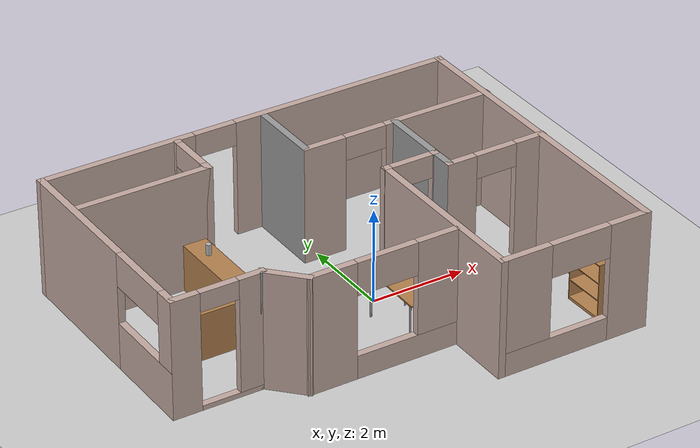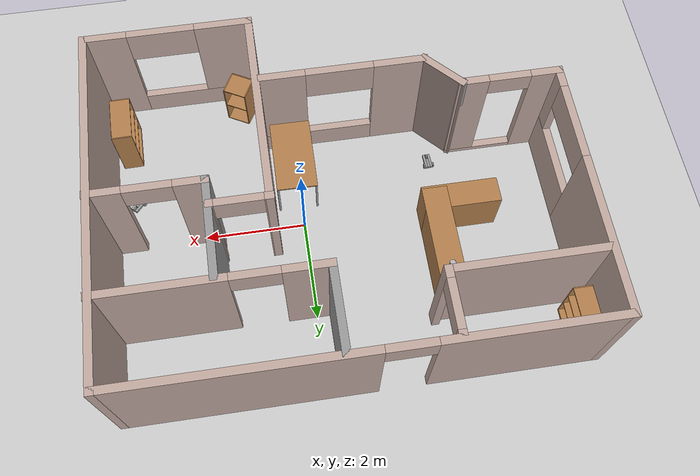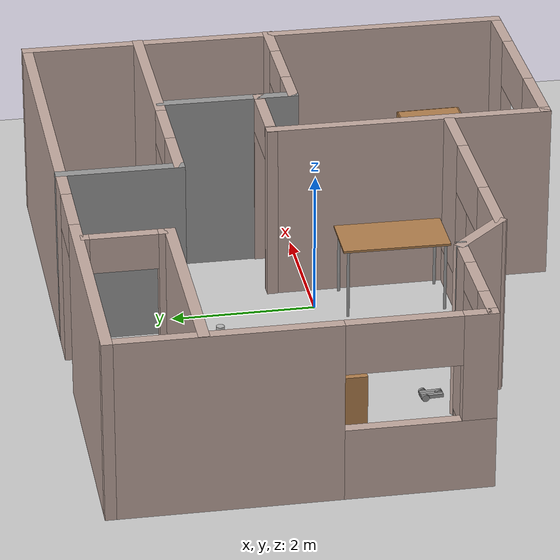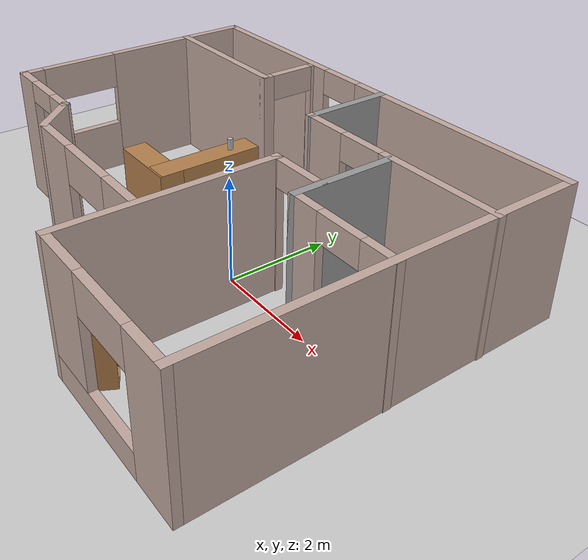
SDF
<sdf version="1.6">
 <world name="default">
  <plugin name="hello" filename="libhello.so"/>
  <light name="sun" type="directional">
   <pose>0 0 10 0 -0 0</pose>
   <diffuse>0.8 0.8 0.8 1</diffuse>
   <specular>0.2 0.2 0.2 1</specular>
   <attenuation>
    <range>1000</range>
    <constant>0.9</constant>
    <linear>0.01</linear>
    <quadratic>0.001</quadratic>
   </attenuation>
   <direction>-0.5 0.1 -0.9</direction>
  </light>
  <model name="ground_plane">
   <static>1</static>
   <link name="link">
    <collision name="collision">
     <geometry><plane><normal>0 0 1</normal><size>100 100</size></plane></geometry>
     <surface><friction><ode><mu>100</mu><mu2>50</mu2></ode></friction></surface>
    </collision>
    <visual name="visual">
     <cast_shadows>0</cast_shadows>
     <geometry><plane><normal>0 0 1</normal><size>100 100</size></plane></geometry>
     <material>
      <script><uri>file://media/materials/scripts/gazebo.material</uri><name>Gazebo/Grey</name></script>
     </material>
    </visual>
   </link>
  </model>
  <gravity>0 0 -9.8</gravity>
  <magnetic_field>6e-06 2.3e-05 -4.2e-05</magnetic_field>
  <atmosphere type="adiabatic"/>
  <physics name="default_physics" default="0" type="ode">
   <max_step_size>0.001</max_step_size>
   <real_time_factor>1</real_time_factor>
   <real_time_update_rate>1000</real_time_update_rate>
  </physics>
  <scene><ambient>0.4 0.4 0.4 1</ambient><background>0.7 0.7 0.7 1</background><shadows>1</shadows></scene>
  <spherical_coordinates>
   <surface_model>EARTH_WGS84</surface_model>
   <latitude_deg>0</latitude_deg>
   <longitude_deg>0</longitude_deg>
   <elevation>0</elevation>
   <heading_deg>0</heading_deg>
  </spherical_coordinates>
  <model name="Building">
   <pose>-0.641845 0.088842 0 0 -0 0</pose>
   <link name="Wall_0">
    <pose>-0.008719 3.42505 0 0 -0 0</pose>
    <visual name="Wall_0_Visual_0">
     <pose>-2.83723 0 1.25 0 -0 0</pose>
     <geometry><box><size>3.32554 0.15 2.5</size></box></geometry>
     <material>
      <script><uri>file://media/materials/scripts/gazebo.material</uri><name>Gazebo/Grey</name></script>
      <ambient>0.760784 0.662745 0.627451 1</ambient>
     </material>
     <meta><layer>0</layer></meta>
    </visual>
    <collision name="Wall_0_Collision_0">
     <geometry><box><size>3.32554 0.15 2.5</size></box></geometry>
     <pose>-2.83723 0 1.25 0 -0 0</pose>
    </collision>
    <visual name="Wall_0_Visual_1">
     <pose>2.11277 0 1.25 0 -0 0</pose>
     <geometry><box><size>4.77445 0.15 2.5</size></box></geometry>
     <material>
      <script><uri>file://media/materials/scripts/gazebo.material</uri><name>Gazebo/Grey</name></script>
      <ambient>0.760784 0.662745 0.627451 1</ambient>
     </material>
     <meta><layer>0</layer></meta>
    </visual>
    <collision name="Wall_0_Collision_1">
     <geometry><box><size>4.77445 0.15 2.5</size></box></geometry>
     <pose>2.11277 0 1.25 0 -0 0</pose>
    </collision>
    <visual name="Wall_0_Visual_2">
     <pose>-0.724455 0 2.25 0 -0 0</pose>
     <geometry><box><size>0.9 0.15 0.5</size></box></geometry>
     <material>
      <script><uri>file://media/materials/scripts/gazebo.material</uri><name>Gazebo/Grey</name></script>
      <ambient>0.760784 0.662745 0.627451 1</ambient>
     </material>
     <meta><layer>0</layer></meta>
    </visual>
    <collision name="Wall_0_Collision_2">
     <geometry><box><size>0.9 0.15 0.5</size></box></geometry>
     <pose>-0.724455 0 2.25 0 -0 0</pose>
    </collision>
   </link>
   <link name="Wall_17">
    <collision name="Wall_17_Collision">
     <geometry><box><size>7 0.15 2.5</size></box></geometry>
     <pose>0 0 1.25 0 -0 0</pose>
    </collision>
    <visual name="Wall_17_Visual">
     <pose>0 0 1.25 0 -0 0</pose>
     <geometry><box><size>7 0.15 2.5</size></box></geometry>
     <material>
      <script><uri>file://media/materials/scripts/gazebo.material</uri><name>Gazebo/Grey</name></script>
      <ambient>0.760784 0.662745 0.627451 1</ambient>
     </material>
     <meta><layer>0</layer></meta>
    </visual>
    <pose>4.41628 5.1e-05 0 0 0 -1.5708</pose>
   </link>
   <link name="Wall_19">
    <pose>2.83077 -3.42495 0 0 -0 3.14159</pose>
    <visual name="Wall_19_Visual_0">
     <pose>-1.20755 0 1.25 0 -0 0</pose>
     <geometry><box><size>0.905905 0.15 2.5</size></box></geometry>
     <material>
      <script><uri>file://media/materials/scripts/gazebo.material</uri><name>Gazebo/Grey</name></script>
      <ambient>0.760784 0.662745 0.627451 1</ambient>
     </material>
     <meta><layer>0</layer></meta>
    </visual>
    <collision name="Wall_19_Collision_0">
     <geometry><box><size>0.905905 0.15 2.5</size></box></geometry>
     <pose>-1.20755 0 1.25 0 -0 0</pose>
    </collision>
    <visual name="Wall_19_Visual_1">
     <pose>0.452953 0 0.25 0 -0 0</pose>
     <geometry><box><size>2.41511 0.15 0.5</size></box></geometry>
     <material>
      <script><uri>file://media/materials/scripts/gazebo.material</uri><name>Gazebo/Grey</name></script>
      <ambient>0.760784 0.662745 0.627451 1</ambient>
     </material>
     <meta><layer>0</layer></meta>
    </visual>
    <collision name="Wall_19_Collision_1">
     <geometry><box><size>2.41511 0.15 0.5</size></box></geometry>
     <pose>0.452953 0 0.25 0 -0 0</pose>
    </collision>
    <visual name="Wall_19_Visual_2">
     <pose>1.10295 0 1.5 0 -0 0</pose>
     <geometry><box><size>1.11511 0.15 2</size></box></geometry>
     <material>
      <script><uri>file://media/materials/scripts/gazebo.material</uri><name>Gazebo/Grey</name></script>
      <ambient>0.760784 0.662745 0.627451 1</ambient>
     </material>
     <meta><layer>0</layer></meta>
    </visual>
    <collision name="Wall_19_Collision_2">
     <geometry><box><size>1.11511 0.15 2</size></box></geometry>
     <pose>1.10295 0 1.5 0 -0 0</pose>
    </collision>
    <visual name="Wall_19_Visual_3">
     <pose>-0.104603 0 2.15 0 -0 0</pose>
     <geometry><box><size>1.3 0.15 0.7</size></box></geometry>
     <material>
      <script><uri>file://media/materials/scripts/gazebo.material</uri><name>Gazebo/Grey</name></script>
      <ambient>0.760784 0.662745 0.627451 1</ambient>
     </material>
     <meta><layer>0</layer></meta>
    </visual>
    <collision name="Wall_19_Collision_3">
     <geometry><box><size>1.3 0.15 0.7</size></box></geometry>
     <pose>-0.104603 0 2.15 0 -0 0</pose>
    </collision>
   </link>
   <link name="Wall_23">
    <pose>-3.50872 -1.42495 0 0 -0 0</pose>
    <visual name="Wall_23_Visual_0">
     <pose>-0.693942 0 1.25 0 -0 0</pose>
     <geometry><box><size>0.612115 0.15 2.5</size></box></geometry>
     <material>
      <script><uri>file://media/materials/scripts/gazebo.material</uri><name>Gazebo/Grey</name></script>
      <ambient>0.760784 0.662745 0.627451 1</ambient>
     </material>
     <meta><layer>0</layer></meta>
    </visual>
    <collision name="Wall_23_Collision_0">
     <geometry><box><size>0.612115 0.15 2.5</size></box></geometry>
     <pose>-0.693942 0 1.25 0 -0 0</pose>
    </collision>
    <visual name="Wall_23_Visual_1">
     <pose>0.306058 0 0.05 0 -0 0</pose>
     <geometry><box><size>1.38789 0.15 0.1</size></box></geometry>
     <material>
      <script><uri>file://media/materials/scripts/gazebo.material</uri><name>Gazebo/Grey</name></script>
      <ambient>0.760784 0.662745 0.627451 1</ambient>
     </material>
     <meta><layer>0</layer></meta>
    </visual>
    <collision name="Wall_23_Collision_1">
     <geometry><box><size>1.38789 0.15 0.1</size></box></geometry>
     <pose>0.306058 0 0.05 0 -0 0</pose>
    </collision>
    <visual name="Wall_23_Visual_2">
     <pose>0.706058 0 1.3 0 -0 0</pose>
     <geometry><box><size>0.587885 0.15 2.4</size></box></geometry>
     <material>
      <script><uri>file://media/materials/scripts/gazebo.material</uri><name>Gazebo/Grey</name></script>
      <ambient>0.760784 0.662745 0.627451 1</ambient>
     </material>
     <meta><layer>0</layer></meta>
    </visual>
    <collision name="Wall_23_Collision_2">
     <geometry><box><size>0.587885 0.15 2.4</size></box></geometry>
     <pose>0.706058 0 1.3 0 -0 0</pose>
    </collision>
    <visual name="Wall_23_Visual_3">
     <pose>0.012115 0 2.3 0 -0 0</pose>
     <geometry><box><size>0.8 0.15 0.4</size></box></geometry>
     <material>
      <script><uri>file://media/materials/scripts/gazebo.material</uri><name>Gazebo/Grey</name></script>
      <ambient>0.760784 0.662745 0.627451 1</ambient>
     </material>
     <meta><layer>0</layer></meta>
    </visual>
    <collision name="Wall_23_Collision_3">
     <geometry><box><size>0.8 0.15 0.4</size></box></geometry>
     <pose>0.012115 0 2.3 0 -0 0</pose>
    </collision>
   </link>
   <link name="Wall_24">
    <collision name="Wall_24_Collision">
     <geometry><box><size>1.02135 0.15 2.5</size></box></geometry>
     <pose>0 0 1.25 0 -0 0</pose>
    </collision>
    <visual name="Wall_24_Visual">
     <pose>0 0 1.25 0 -0 0</pose>
     <geometry><box><size>1.02135 0.15 2.5</size></box></geometry>
     <material>
      <script><uri>file://media/materials/scripts/gazebo.material</uri><name>Gazebo/Grey</name></script>
      <ambient>0.760784 0.662745 0.627451 1</ambient>
     </material>
     <meta><layer>0</layer></meta>
    </visual>
    <pose>-2.2832 -1.74038 0 0 0 -0.809608</pose>
   </link>
   <link name="Wall_27">
    <collision name="Wall_27_Collision">
     <geometry><box><size>1.75 0.15 2.5</size></box></geometry>
     <pose>0 0 1.25 0 -0 0</pose>
    </collision>
    <visual name="Wall_27_Visual">
     <pose>0 0 1.25 0 -0 0</pose>
     <geometry><box><size>1.75 0.15 2.5</size></box></geometry>
     <material>
      <script><uri>file://media/materials/scripts/gazebo.material</uri><name>Gazebo/Grey</name></script>
      <ambient>1 1 1 1</ambient>
     </material>
     <meta><layer>0</layer></meta>
    </visual>
    <pose>0.33372 2.62505 0 0 0 -1.5708</pose>
   </link>
   <link name="Wall_28">
    <pose>2.38372 1.82505 0 0 -0 0</pose>
    <visual name="Wall_28_Visual_0">
     <pose>-1.65584 0 1.25 0 -0 0</pose>
     <geometry><box><size>0.93832 0.15 2.5</size></box></geometry>
     <material>
      <script><uri>file://media/materials/scripts/gazebo.material</uri><name>Gazebo/Grey</name></script>
      <ambient>0.760784 0.662745 0.627451 1</ambient>
     </material>
     <meta><layer>0</layer></meta>
    </visual>
    <collision name="Wall_28_Collision_0">
     <geometry><box><size>0.93832 0.15 2.5</size></box></geometry>
     <pose>-1.65584 0 1.25 0 -0 0</pose>
    </collision>
    <visual name="Wall_28_Visual_1">
     <pose>0.91916 0 1.25 0 -0 0</pose>
     <geometry><box><size>2.41168 0.15 2.5</size></box></geometry>
     <material>
      <script><uri>file://media/materials/scripts/gazebo.material</uri><name>Gazebo/Grey</name></script>
      <ambient>0.760784 0.662745 0.627451 1</ambient>
     </material>
     <meta><layer>0</layer></meta>
    </visual>
    <collision name="Wall_28_Collision_1">
     <geometry><box><size>2.41168 0.15 2.5</size></box></geometry>
     <pose>0.91916 0 1.25 0 -0 0</pose>
    </collision>
    <visual name="Wall_28_Visual_2">
     <pose>-0.73668 0 2.25 0 -0 0</pose>
     <geometry><box><size>0.9 0.15 0.5</size></box></geometry>
     <material>
      <script><uri>file://media/materials/scripts/gazebo.material</uri><name>Gazebo/Grey</name></script>
      <ambient>0.760784 0.662745 0.627451 1</ambient>
     </material>
     <meta><layer>0</layer></meta>
    </visual>
    <collision name="Wall_28_Collision_2">
     <geometry><box><size>0.9 0.15 0.5</size></box></geometry>
     <pose>-0.73668 0 2.25 0 -0 0</pose>
    </collision>
   </link>
   <link name="Wall_30">
    <collision name="Wall_30_Collision">
     <geometry><box><size>2 0.15 2.5</size></box></geometry>
     <pose>0 0 1.25 0 -0 0</pose>
    </collision>
    <visual name="Wall_30_Visual">
     <pose>0 0 1.25 0 -0 0</pose>
     <geometry><box><size>2 0.15 2.5</size></box></geometry>
     <material>
      <script><uri>file://media/materials/scripts/gazebo.material</uri><name>Gazebo/Grey</name></script>
      <ambient>1 1 1 1</ambient>
     </material>
     <meta><layer>0</layer></meta>
    </visual>
    <pose>2.32759 0.85598 0 0 0 -1.5708</pose>
   </link>
   <link name="Wall_32">
    <pose>3.37759 -0.06902 0 0 -0 0</pose>
    <visual name="Wall_32_Visual_0">
     <pose>-0.796543 0 1.25 0 -0 0</pose>
     <geometry><box><size>0.656914 0.15 2.5</size></box></geometry>
     <material>
      <script><uri>file://media/materials/scripts/gazebo.material</uri><name>Gazebo/Grey</name></script>
      <ambient>0.760784 0.662745 0.627451 1</ambient>
     </material>
     <meta><layer>0</layer></meta>
    </visual>
    <collision name="Wall_32_Collision_0">
     <geometry><box><size>0.656914 0.15 2.5</size></box></geometry>
     <pose>-0.796543 0 1.25 0 -0 0</pose>
    </collision>
    <visual name="Wall_32_Visual_1">
     <pose>0.778457 0 1.25 0 -0 0</pose>
     <geometry><box><size>0.693086 0.15 2.5</size></box></geometry>
     <material>
      <script><uri>file://media/materials/scripts/gazebo.material</uri><name>Gazebo/Grey</name></script>
      <ambient>0.760784 0.662745 0.627451 1</ambient>
     </material>
     <meta><layer>0</layer></meta>
    </visual>
    <collision name="Wall_32_Collision_1">
     <geometry><box><size>0.693086 0.15 2.5</size></box></geometry>
     <pose>0.778457 0 1.25 0 -0 0</pose>
    </collision>
    <visual name="Wall_32_Visual_2">
     <pose>-0.018086 0 2.25 0 -0 0</pose>
     <geometry><box><size>0.9 0.15 0.5</size></box></geometry>
     <material>
      <script><uri>file://media/materials/scripts/gazebo.material</uri><name>Gazebo/Grey</name></script>
      <ambient>0.760784 0.662745 0.627451 1</ambient>
     </material>
     <meta><layer>0</layer></meta>
    </visual>
    <collision name="Wall_32_Collision_2">
     <geometry><box><size>0.9 0.15 0.5</size></box></geometry>
     <pose>-0.018086 0 2.25 0 -0 0</pose>
    </collision>
   </link>
   <link name="Wall_34">
    <collision name="Wall_34_Collision">
     <geometry><box><size>3 0.15 2.5</size></box></geometry>
     <pose>0 0 1.25 0 -0 0</pose>
    </collision>
    <visual name="Wall_34_Visual">
     <pose>0 0 1.25 0 -0 0</pose>
     <geometry><box><size>3 0.15 2.5</size></box></geometry>
     <material>
      <script><uri>file://media/materials/scripts/gazebo.material</uri><name>Gazebo/Grey</name></script>
      <ambient>0.760784 0.662745 0.627451 1</ambient>
     </material>
     <meta><layer>0</layer></meta>
    </visual>
    <pose>-2.99858 2.21823 0 0 -0 0</pose>
   </link>
   <link name="Wall_35">
    <pose>-1.57358 2.76823 0 0 -0 1.5708</pose>
    <visual name="Wall_35_Visual_0">
     <pose>-0.506424 0 1.25 0 -0 0</pose>
     <geometry><box><size>0.237152 0.15 2.5</size></box></geometry>
     <material>
      <script><uri>file://media/materials/scripts/gazebo.material</uri><name>Gazebo/Grey</name></script>
      <ambient>0.760784 0.662745 0.627451 1</ambient>
     </material>
     <meta><layer>0</layer></meta>
    </visual>
    <collision name="Wall_35_Collision_0">
     <geometry><box><size>0.237152 0.15 2.5</size></box></geometry>
     <pose>-0.506424 0 1.25 0 -0 0</pose>
    </collision>
    <visual name="Wall_35_Visual_1">
     <pose>0.568576 0 1.25 0 -0 0</pose>
     <geometry><box><size>0.112848 0.15 2.5</size></box></geometry>
     <material>
      <script><uri>file://media/materials/scripts/gazebo.material</uri><name>Gazebo/Grey</name></script>
      <ambient>0.760784 0.662745 0.627451 1</ambient>
     </material>
     <meta><layer>0</layer></meta>
    </visual>
    <collision name="Wall_35_Collision_1">
     <geometry><box><size>0.112848 0.15 2.5</size></box></geometry>
     <pose>0.568576 0 1.25 0 -0 0</pose>
    </collision>
    <visual name="Wall_35_Visual_2">
     <pose>0.062152 0 2.25 0 -0 0</pose>
     <geometry><box><size>0.9 0.15 0.5</size></box></geometry>
     <material>
      <script><uri>file://media/materials/scripts/gazebo.material</uri><name>Gazebo/Grey</name></script>
      <ambient>0.760784 0.662745 0.627451 1</ambient>
     </material>
     <meta><layer>0</layer></meta>
    </visual>
    <collision name="Wall_35_Collision_2">
     <geometry><box><size>0.9 0.15 0.5</size></box></geometry>
     <pose>0.062152 0 2.25 0 -0 0</pose>
    </collision>
   </link>
   <link name="Wall_37">
    <collision name="Wall_37_Collision">
     <geometry><box><size>3.99026 0.15 2.5</size></box></geometry>
     <pose>0 0 1.25 0 -0 0</pose>
    </collision>
    <visual name="Wall_37_Visual">
     <pose>0 0 1.25 0 -0 0</pose>
     <geometry><box><size>3.99026 0.15 2.5</size></box></geometry>
     <material>
      <script><uri>file://media/materials/scripts/gazebo.material</uri><name>Gazebo/Grey</name></script>
      <ambient>0.760784 0.662745 0.627451 1</ambient>
     </material>
     <meta><layer>0</layer></meta>
    </visual>
    <pose>1.23533 -1.50492 0 0 -0 1.57079</pose>
   </link>
   <link name="Wall_38">
    <pose>1.77039 0.415108 0 0 -0 0</pose>
    <visual name="Wall_38_Visual_0">
     <pose>-0.529272 0 1.25 0 -0 0</pose>
     <geometry><box><size>0.181455 0.15 2.5</size></box></geometry>
     <material>
      <script><uri>file://media/materials/scripts/gazebo.material</uri><name>Gazebo/Grey</name></script>
      <ambient>0.760784 0.662745 0.627451 1</ambient>
     </material>
     <meta><layer>0</layer></meta>
    </visual>
    <collision name="Wall_38_Collision_0">
     <geometry><box><size>0.181455 0.15 2.5</size></box></geometry>
     <pose>-0.529272 0 1.25 0 -0 0</pose>
    </collision>
    <visual name="Wall_38_Visual_1">
     <pose>0.540728 0 1.25 0 -0 0</pose>
     <geometry><box><size>0.158545 0.15 2.5</size></box></geometry>
     <material>
      <script><uri>file://media/materials/scripts/gazebo.material</uri><name>Gazebo/Grey</name></script>
      <ambient>0.760784 0.662745 0.627451 1</ambient>
     </material>
     <meta><layer>0</layer></meta>
    </visual>
    <collision name="Wall_38_Collision_1">
     <geometry><box><size>0.158545 0.15 2.5</size></box></geometry>
     <pose>0.540728 0 1.25 0 -0 0</pose>
    </collision>
    <visual name="Wall_38_Visual_2">
     <pose>0.011455 0 2.25 0 -0 0</pose>
     <geometry><box><size>0.9 0.15 0.5</size></box></geometry>
     <material>
      <script><uri>file://media/materials/scripts/gazebo.material</uri><name>Gazebo/Grey</name></script>
      <ambient>0.760784 0.662745 0.627451 1</ambient>
     </material>
     <meta><layer>0</layer></meta>
    </visual>
    <collision name="Wall_38_Collision_2">
     <geometry><box><size>0.9 0.15 0.5</size></box></geometry>
     <pose>0.011455 0 2.25 0 -0 0</pose>
    </collision>
   </link>
   <link name="Wall_4">
    <pose>-4.43372 1.00005 0 0 0 -1.5708</pose>
    <visual name="Wall_4_Visual_0">
     <pose>-0.974806 0 1.25 0 -0 0</pose>
     <geometry><box><size>3.05039 0.15 2.5</size></box></geometry>
     <material>
      <script><uri>file://media/materials/scripts/gazebo.material</uri><name>Gazebo/Grey</name></script>
      <ambient>0.760784 0.662745 0.627451 1</ambient>
     </material>
     <meta><layer>0</layer></meta>
    </visual>
    <collision name="Wall_4_Collision_0">
     <geometry><box><size>3.05039 0.15 2.5</size></box></geometry>
     <pose>-0.974806 0 1.25 0 -0 0</pose>
    </collision>
    <visual name="Wall_4_Visual_1">
     <pose>1.52519 0 0.5 0 -0 0</pose>
     <geometry><box><size>1.94961 0.15 1</size></box></geometry>
     <material>
      <script><uri>file://media/materials/scripts/gazebo.material</uri><name>Gazebo/Grey</name></script>
      <ambient>0.760784 0.662745 0.627451 1</ambient>
     </material>
     <meta><layer>0</layer></meta>
    </visual>
    <collision name="Wall_4_Collision_1">
     <geometry><box><size>1.94961 0.15 1</size></box></geometry>
     <pose>1.52519 0 0.5 0 -0 0</pose>
    </collision>
    <visual name="Wall_4_Visual_2">
     <pose>2.27519 0 1.75 0 -0 0</pose>
     <geometry><box><size>0.449611 0.15 1.5</size></box></geometry>
     <material>
      <script><uri>file://media/materials/scripts/gazebo.material</uri><name>Gazebo/Grey</name></script>
      <ambient>0.760784 0.662745 0.627451 1</ambient>
     </material>
     <meta><layer>0</layer></meta>
    </visual>
    <collision name="Wall_4_Collision_2">
     <geometry><box><size>0.449611 0.15 1.5</size></box></geometry>
     <pose>2.27519 0 1.75 0 -0 0</pose>
    </collision>
    <visual name="Wall_4_Visual_3">
     <pose>1.30039 0 2.15 0 -0 0</pose>
     <geometry><box><size>1.5 0.15 0.7</size></box></geometry>
     <material>
      <script><uri>file://media/materials/scripts/gazebo.material</uri><name>Gazebo/Grey</name></script>
      <ambient>0.760784 0.662745 0.627451 1</ambient>
     </material>
     <meta><layer>0</layer></meta>
    </visual>
    <collision name="Wall_4_Collision_3">
     <geometry><box><size>1.5 0.15 0.7</size></box></geometry>
     <pose>1.30039 0 2.15 0 -0 0</pose>
    </collision>
   </link>
   <link name="Wall_40">
    <pose>-0.432678 -2.05582 0 0 -0 0</pose>
    <visual name="Wall_40_Visual_0">
     <pose>-1.09985 0 1.25 0 -0 0</pose>
     <geometry><box><size>1.0503 0.15 2.5</size></box></geometry>
     <material>
      <script><uri>file://media/materials/scripts/gazebo.material</uri><name>Gazebo/Grey</name></script>
      <ambient>0.760784 0.662745 0.627451 1</ambient>
     </material>
     <meta><layer>0</layer></meta>
    </visual>
    <collision name="Wall_40_Collision_0">
     <geometry><box><size>1.0503 0.15 2.5</size></box></geometry>
     <pose>-1.09985 0 1.25 0 -0 0</pose>
    </collision>
    <visual name="Wall_40_Visual_1">
     <pose>0.52515 0 0.25 0 -0 0</pose>
     <geometry><box><size>2.1997 0.15 0.5</size></box></geometry>
     <material>
      <script><uri>file://media/materials/scripts/gazebo.material</uri><name>Gazebo/Grey</name></script>
      <ambient>0.760784 0.662745 0.627451 1</ambient>
     </material>
     <meta><layer>0</layer></meta>
    </visual>
    <collision name="Wall_40_Collision_1">
     <geometry><box><size>2.1997 0.15 0.5</size></box></geometry>
     <pose>0.52515 0 0.25 0 -0 0</pose>
    </collision>
    <visual name="Wall_40_Visual_2">
     <pose>1.17515 0 1.5 0 -0 0</pose>
     <geometry><box><size>0.8997 0.15 2</size></box></geometry>
     <material>
      <script><uri>file://media/materials/scripts/gazebo.material</uri><name>Gazebo/Grey</name></script>
      <ambient>0.760784 0.662745 0.627451 1</ambient>
     </material>
     <meta><layer>0</layer></meta>
    </visual>
    <collision name="Wall_40_Collision_2">
     <geometry><box><size>0.8997 0.15 2</size></box></geometry>
     <pose>1.17515 0 1.5 0 -0 0</pose>
    </collision>
    <visual name="Wall_40_Visual_3">
     <pose>0.0753 0 2.15 0 -0 0</pose>
     <geometry><box><size>1.3 0.15 0.7</size></box></geometry>
     <material>
      <script><uri>file://media/materials/scripts/gazebo.material</uri><name>Gazebo/Grey</name></script>
      <ambient>0.760784 0.662745 0.627451 1</ambient>
     </material>
     <meta><layer>0</layer></meta>
    </visual>
    <collision name="Wall_40_Collision_3">
     <geometry><box><size>1.3 0.15 0.7</size></box></geometry>
     <pose>0.0753 0 2.15 0 -0 0</pose>
    </collision>
   </link>
   <link name="Wall_42">
    <collision name="Wall_42_Collision">
     <geometry><box><size>2.25 0.5 1</size></box></geometry>
     <pose>0 0 0.5 0 -0 0</pose>
    </collision>
    <visual name="Wall_42_Visual">
     <pose>0 0 0.5 0 -0 0</pose>
     <geometry><box><size>2.25 0.5 1</size></box></geometry>
     <material>
      <script><uri>file://media/materials/scripts/gazebo.material</uri><name>Gazebo/Wood</name></script>
      <ambient>1 1 1 1</ambient>
     </material>
     <meta><layer>0</layer></meta>
    </visual>
    <pose>-1.93472 1.06205 0 0 0 -1.5708</pose>
   </link>
   <link name="Wall_44">
    <collision name="Wall_44_Collision">
     <geometry><box><size>1.5 0.5 1</size></box></geometry>
     <pose>0 0 0.5 0 -0 0</pose>
    </collision>
    <visual name="Wall_44_Visual">
     <pose>0 0 0.5 0 -0 0</pose>
     <geometry><box><size>1.5 0.5 1</size></box></geometry>
     <material>
      <script><uri>file://media/materials/scripts/gazebo.material</uri><name>Gazebo/Wood</name></script>
      <ambient>1 1 1 1</ambient>
     </material>
     <meta><layer>0</layer></meta>
    </visual>
    <pose>-2.43272 0.148052 0 0 -0 3.14159</pose>
   </link>
   <link name="Wall_6">
    <collision name="Wall_6_Collision">
     <geometry><box><size>0.15 0.15 2.5</size></box></geometry>
     <pose>0 0 1.25 0 -0 0</pose>
    </collision>
    <visual name="Wall_6_Visual">
     <pose>0 0 1.25 0 -0 0</pose>
     <geometry><box><size>0.15 0.15 2.5</size></box></geometry>
     <material>
      <script><uri>file://media/materials/scripts/gazebo.material</uri><name>Gazebo/Grey</name></script>
      <ambient>1 1 1 1</ambient>
     </material>
     <meta><layer>0</layer></meta>
    </visual>
    <pose>-2.58372 -1.42495 0 0 -0 0</pose>
   </link>
   <static>1</static>
  </model>
  <model name="beer">
   <link name="link">
    <pose>0 0 0.115 0 -0 0</pose>
    <inertial>
     <mass>0.39</mass>
     <inertia><ixx>0.00058</ixx><ixy>0</ixy><ixz>0</ixz><iyy>0.00058</iyy><iyz>0</iyz><izz>0.00019</izz></inertia>
    </inertial>
    <collision name="collision">
     <geometry><cylinder><radius>0.055</radius><length>0.23</length></cylinder></geometry>
    </collision>
    <visual name="visual">
     <geometry><cylinder><radius>0.055</radius><length>0.23</length></cylinder></geometry>
     <material>
      <script>
       <uri>model://beer/materials/scripts</uri>
       <uri>model://beer/materials/textures</uri>
       <name>Beer/Diffuse</name>
      </script>
     </material>
    </visual>
   </link>
   <pose>-2.56948 1.71503 1.00001 2.5e-05 9.5e-05 -0.000763</pose>
  </model>
  <model name="table">
   <static>1</static>
   <link name="link">
    <collision name="surface">
     <pose>0 0 1 0 -0 0</pose>
     <geometry><box><size>1.5 0.8 0.03</size></box></geometry>
     <surface><friction><ode><mu>0.6</mu><mu2>0.6</mu2></ode></friction></surface>
    </collision>
    <visual name="visual1">
     <pose>0 0 1 0 -0 0</pose>
     <geometry><box><size>1.5 0.8 0.03</size></box></geometry>
     <material>
      <script><uri>file://media/materials/scripts/gazebo.material</uri><name>Gazebo/Wood</name></script>
     </material>
    </visual>
    <collision name="front_left_leg">
     <pose>0.68 0.38 0.5 0 -0 0</pose>
     <geometry><cylinder><radius>0.02</radius><length>1</length></cylinder></geometry>
    </collision>
    <visual name="front_left_leg">
     <pose>0.68 0.38 0.5 0 -0 0</pose>
     <geometry><cylinder><radius>0.02</radius><length>1</length></cylinder></geometry>
     <material>
      <script><uri>file://media/materials/scripts/gazebo.material</uri><name>Gazebo/Grey</name></script>
     </material>
    </visual>
    <collision name="front_right_leg">
     <pose>0.68 -0.38 0.5 0 -0 0</pose>
     <geometry><cylinder><radius>0.02</radius><length>1</length></cylinder></geometry>
    </collision>
    <visual name="front_right_leg">
     <pose>0.68 -0.38 0.5 0 -0 0</pose>
     <geometry><cylinder><radius>0.02</radius><length>1</length></cylinder></geometry>
     <material>
      <script><uri>file://media/materials/scripts/gazebo.material</uri><name>Gazebo/Grey</name></script>
     </material>
    </visual>
    <collision name="back_right_leg">
     <pose>-0.68 -0.38 0.5 0 -0 0</pose>
     <geometry><cylinder><radius>0.02</radius><length>1</length></cylinder></geometry>
    </collision>
    <visual name="back_right_leg">
     <pose>-0.68 -0.38 0.5 0 -0 0</pose>
     <geometry><cylinder><radius>0.02</radius><length>1</length></cylinder></geometry>
     <material>
      <script><uri>file://media/materials/scripts/gazebo.material</uri><name>Gazebo/Grey</name></script>
     </material>
    </visual>
    <collision name="back_left_leg">
     <pose>-0.68 0.38 0.5 0 -0 0</pose>
     <geometry><cylinder><radius>0.02</radius><length>1</length></cylinder></geometry>
    </collision>
    <visual name="back_left_leg">
     <pose>-0.68 0.38 0.5 0 -0 0</pose>
     <geometry><cylinder><radius>0.02</radius><length>1</length></cylinder></geometry>
     <material>
      <script><uri>file://media/materials/scripts/gazebo.material</uri><name>Gazebo/Grey</name></script>
     </material>
    </visual>
   </link>
   <pose>0.053466 -1.09473 0 0 0 -1.58225</pose>
  </model>
  <model name="bookshelf">
   <static>1</static>
   <link name="link">
    <inertial><mass>1</mass></inertial>
    <collision name="back">
     <pose>0 0.005 0.6 0 -0 0</pose>
     <geometry><box><size>0.9 0.01 1.2</size></box></geometry>
    </collision>
    <visual name="visual1">
     <pose>0 0.005 0.6 0 -0 0</pose>
     <geometry><box><size>0.9 0.01 1.2</size></box></geometry>
     <material>
      <script><uri>file://media/materials/scripts/gazebo.material</uri><name>Gazebo/Wood</name></script>
     </material>
    </visual>
    <collision name="left_side">
     <pose>0.45 -0.195 0.6 0 -0 0</pose>
     <geometry><box><size>0.02 0.4 1.2</size></box></geometry>
    </collision>
    <visual name="visual2">
     <pose>0.45 -0.195 0.6 0 -0 0</pose>
     <geometry><box><size>0.02 0.4 1.2</size></box></geometry>
     <material>
      <script><uri>file://media/materials/scripts/gazebo.material</uri><name>Gazebo/Wood</name></script>
     </material>
    </visual>
    <collision name="right_side">
     <pose>-0.45 -0.195 0.6 0 -0 0</pose>
     <geometry><box><size>0.02 0.4 1.2</size></box></geometry>
    </collision>
    <visual name="visual3">
     <pose>-0.45 -0.195 0.6 0 -0 0</pose>
     <geometry><box><size>0.02 0.4 1.2</size></box></geometry>
     <material>
      <script><uri>file://media/materials/scripts/gazebo.material</uri><name>Gazebo/Wood</name></script>
     </material>
    </visual>
    <collision name="bottom">
     <pose>0 -0.195 0.03 0 -0 0</pose>
     <geometry><box><size>0.88 0.4 0.06</size></box></geometry>
    </collision>
    <visual name="visual4">
     <pose>0 -0.195 0.03 0 -0 0</pose>
     <geometry><box><size>0.88 0.4 0.06</size></box></geometry>
     <material>
      <script><uri>file://media/materials/scripts/gazebo.material</uri><name>Gazebo/Wood</name></script>
     </material>
    </visual>
    <collision name="top">
     <pose>0 -0.195 1.19 0 -0 0</pose>
     <geometry><box><size>0.88 0.4 0.02</size></box></geometry>
    </collision>
    <visual name="visual5">
     <pose>0 -0.195 1.19 0 -0 0</pose>
     <geometry><box><size>0.88 0.4 0.02</size></box></geometry>
     <material>
      <script><uri>file://media/materials/scripts/gazebo.material</uri><name>Gazebo/Wood</name></script>
     </material>
    </visual>
    <collision name="low_shelf">
     <pose>0 -0.195 0.43 0 -0 0</pose>
     <geometry><box><size>0.88 0.4 0.02</size></box></geometry>
    </collision>
    <visual name="visual6">
     <pose>0 -0.195 0.43 0 -0 0</pose>
     <geometry><box><size>0.88 0.4 0.02</size></box></geometry>
     <material>
      <script><uri>file://media/materials/scripts/gazebo.material</uri><name>Gazebo/Wood</name></script>
     </material>
    </visual>
    <collision name="high_shelf">
     <pose>0 -0.195 0.8 0 -0 0</pose>
     <geometry><box><size>0.88 0.4 0.02</size></box></geometry>
    </collision>
    <visual name="visual7">
     <pose>0 -0.195 0.8 0 -0 0</pose>
     <geometry><box><size>0.88 0.4 0.02</size></box></geometry>
     <material>
      <script><uri>file://media/materials/scripts/gazebo.material</uri><name>Gazebo/Wood</name></script>
     </material>
    </visual>
   </link>
   <pose>3.58099 -2.31658 0 0 0 -1.55277</pose>
  </model>
  <model name="tricycle">
   <link name="link_0_clone">
    <pose>0.05011 -0.0238 0 0 -0 0</pose>
    <inertial>
     <mass>1</mass>
     <inertia>
      <ixx>0.166667</ixx>
      <ixy>0</ixy>
      <ixz>0</ixz>
      <iyy>0.166667</iyy>
      <iyz>0</iyz>
      <izz>0.166667</izz>
     </inertia>
    </inertial>
    <visual name="visual">
     <geometry><box><size>0.05 0.3 0.05</size></box></geometry>
     <material>
      <lighting>1</lighting>
      <script><uri>file://media/materials/scripts/gazebo.material</uri><name>Gazebo/Grey</name></script>
      <shader type="pixel"><normal_map>__default__</normal_map></shader>
      <ambient>0.3 0.3 0.3 1</ambient>
      <diffuse>0.7 0.7 0.7 1</diffuse>
      <specular>0.01 0.01 0.01 1</specular>
      <emissive>0 0 0 1</emissive>
     </material>
    </visual>
    <collision name="collision">
     <geometry><box><size>0.05 0.3 0.05</size></box></geometry>
     <surface>
      <friction>
       <ode><mu>1</mu><mu2>1</mu2><fdir1>0 0 0</fdir1><slip1>0</slip1><slip2>0</slip2></ode>
       <torsional>
        <coefficient>1</coefficient>
        <patch_radius>0</patch_radius>
        <surface_radius>0</surface_radius>
        <use_patch_radius>1</use_patch_radius>
        <ode><slip>0</slip></ode>
       </torsional>
      </friction>
      <bounce><restitution_coefficient>0</restitution_coefficient><threshold>1e+06</threshold></bounce>
      <contact>
       <collide_without_contact>0</collide_without_contact>
       <collide_without_contact_bitmask>1</collide_without_contact_bitmask>
       <collide_bitmask>1</collide_bitmask>
       <ode>
        <soft_cfm>0</soft_cfm>
        <soft_erp>0.2</soft_erp>
        <kp>1e+13</kp>
        <kd>1</kd>
        <max_vel>0.01</max_vel>
        <min_depth>0</min_depth>
       </ode>
       <bullet>
        <split_impulse>1</split_impulse>
        <split_impulse_penetration_threshold>-0.01</split_impulse_penetration_threshold>
        <soft_cfm>0</soft_cfm>
        <soft_erp>0.2</soft_erp>
        <kp>1e+13</kp>
        <kd>1</kd>
       </bullet>
      </contact>
     </surface>
    </collision>
   </link>
   <link name="link_0_clone_0">
    <pose>0.00011 0.0262 0 0 -0 0</pose>
    <inertial>
     <mass>1</mass>
     <inertia>
      <ixx>0.166667</ixx>
      <ixy>0</ixy>
      <ixz>0</ixz>
      <iyy>0.166667</iyy>
      <iyz>0</iyz>
      <izz>0.166667</izz>
     </inertia>
    </inertial>
    <visual name="visual">
     <geometry><box><size>0.05 0.2 0.05</size></box></geometry>
     <material>
      <lighting>1</lighting>
      <script><uri>file://media/materials/scripts/gazebo.material</uri><name>Gazebo/Grey</name></script>
      <shader type="pixel"><normal_map>__default__</normal_map></shader>
      <ambient>0.3 0.3 0.3 1</ambient>
      <diffuse>0.7 0.7 0.7 1</diffuse>
      <specular>0.01 0.01 0.01 1</specular>
      <emissive>0 0 0 1</emissive>
     </material>
    </visual>
    <collision name="collision">
     <geometry><box><size>0.05 0.2 0.05</size></box></geometry>
     <surface>
      <friction>
       <ode><mu>1</mu><mu2>1</mu2><fdir1>0 0 0</fdir1><slip1>0</slip1><slip2>0</slip2></ode>
       <torsional>
        <coefficient>1</coefficient>
        <patch_radius>0</patch_radius>
        <surface_radius>0</surface_radius>
        <use_patch_radius>1</use_patch_radius>
        <ode><slip>0</slip></ode>
       </torsional>
      </friction>
      <bounce><restitution_coefficient>0</restitution_coefficient><threshold>1e+06</threshold></bounce>
      <contact>
       <collide_without_contact>0</collide_without_contact>
       <collide_without_contact_bitmask>1</collide_without_contact_bitmask>
       <collide_bitmask>1</collide_bitmask>
       <ode>
        <soft_cfm>0</soft_cfm>
        <soft_erp>0.2</soft_erp>
        <kp>1e+13</kp>
        <kd>1</kd>
        <max_vel>0.01</max_vel>
        <min_depth>0</min_depth>
       </ode>
       <bullet>
        <split_impulse>1</split_impulse>
        <split_impulse_penetration_threshold>-0.01</split_impulse_penetration_threshold>
        <soft_cfm>0</soft_cfm>
        <soft_erp>0.2</soft_erp>
        <kp>1e+13</kp>
        <kd>1</kd>
       </bullet>
      </contact>
     </surface>
    </collision>
   </link>
   <link name="link_0_clone_clone">
    <pose>-0.04989 -0.0238 0 0 -0 0</pose>
    <inertial>
     <mass>1</mass>
     <inertia>
      <ixx>0.166667</ixx>
      <ixy>0</ixy>
      <ixz>0</ixz>
      <iyy>0.166667</iyy>
      <iyz>0</iyz>
      <izz>0.166667</izz>
     </inertia>
    </inertial>
    <visual name="visual">
     <geometry><box><size>0.05 0.3 0.05</size></box></geometry>
     <material>
      <lighting>1</lighting>
      <script><uri>file://media/materials/scripts/gazebo.material</uri><name>Gazebo/Grey</name></script>
      <shader type="pixel"><normal_map>__default__</normal_map></shader>
      <ambient>0.3 0.3 0.3 1</ambient>
      <diffuse>0.7 0.7 0.7 1</diffuse>
      <specular>0.01 0.01 0.01 1</specular>
      <emissive>0 0 0 1</emissive>
     </material>
    </visual>
    <collision name="collision">
     <geometry><box><size>0.05 0.3 0.05</size></box></geometry>
     <surface>
      <friction>
       <ode><mu>1</mu><mu2>1</mu2><fdir1>0 0 0</fdir1><slip1>0</slip1><slip2>0</slip2></ode>
       <torsional>
        <coefficient>1</coefficient>
        <patch_radius>0</patch_radius>
        <surface_radius>0</surface_radius>
        <use_patch_radius>1</use_patch_radius>
        <ode><slip>0</slip></ode>
       </torsional>
      </friction>
      <bounce><restitution_coefficient>0</restitution_coefficient><threshold>1e+06</threshold></bounce>
      <contact>
       <collide_without_contact>0</collide_without_contact>
       <collide_without_contact_bitmask>1</collide_without_contact_bitmask>
       <collide_bitmask>1</collide_bitmask>
       <ode>
        <soft_cfm>0</soft_cfm>
        <soft_erp>0.2</soft_erp>
        <kp>1e+13</kp>
        <kd>1</kd>
        <max_vel>0.01</max_vel>
        <min_depth>0</min_depth>
       </ode>
       <bullet>
        <split_impulse>1</split_impulse>
        <split_impulse_penetration_threshold>-0.01</split_impulse_penetration_threshold>
        <soft_cfm>0</soft_cfm>
        <soft_erp>0.2</soft_erp>
        <kp>1e+13</kp>
        <kd>1</kd>
       </bullet>
      </contact>
     </surface>
    </collision>
   </link>
   <link name="link_1">
    <pose>-0.000551 -0.131 0 0 -0 0</pose>
    <inertial>
     <mass>1</mass>
     <inertia><ixx>0.145833</ixx><ixy>0</ixy><ixz>0</ixz><iyy>0.145833</iyy><iyz>0</iyz><izz>0.125</izz></inertia>
    </inertial>
    <visual name="visual">
     <pose>0 0 0 0 1.5707 0</pose>
     <geometry><cylinder><radius>0.05</radius><length>0.03</length></cylinder></geometry>
     <material>
      <lighting>1</lighting>
      <script><uri>file://media/materials/scripts/gazebo.material</uri><name>Gazebo/Grey</name></script>
      <shader type="pixel"><normal_map>__default__</normal_map></shader>
      <ambient>0.3 0.3 0.3 1</ambient>
      <diffuse>0.7 0.7 0.7 1</diffuse>
      <specular>0.01 0.01 0.01 1</specular>
      <emissive>0 0 0 1</emissive>
     </material>
    </visual>
    <collision name="collision">
     <pose>0 0 0 0 1.5707 0</pose>
     <geometry><cylinder><radius>0.05</radius><length>0.03</length></cylinder></geometry>
     <surface>
      <friction>
       <ode><mu>1</mu><mu2>1</mu2><fdir1>0 0 0</fdir1><slip1>0</slip1><slip2>0</slip2></ode>
       <torsional>
        <coefficient>1</coefficient>
        <patch_radius>0</patch_radius>
        <surface_radius>0</surface_radius>
        <use_patch_radius>1</use_patch_radius>
        <ode><slip>0</slip></ode>
       </torsional>
      </friction>
      <bounce><restitution_coefficient>0</restitution_coefficient><threshold>1e+06</threshold></bounce>
      <contact>
       <collide_without_contact>0</collide_without_contact>
       <collide_without_contact_bitmask>1</collide_without_contact_bitmask>
       <collide_bitmask>1</collide_bitmask>
       <ode>
        <soft_cfm>0</soft_cfm>
        <soft_erp>0.2</soft_erp>
        <kp>1e+13</kp>
        <kd>1</kd>
        <max_vel>0.01</max_vel>
        <min_depth>0</min_depth>
       </ode>
       <bullet>
        <split_impulse>1</split_impulse>
        <split_impulse_penetration_threshold>-0.01</split_impulse_penetration_threshold>
        <soft_cfm>0</soft_cfm>
        <soft_erp>0.2</soft_erp>
        <kp>1e+13</kp>
        <kd>1</kd>
       </bullet>
      </contact>
     </surface>
    </collision>
   </link>
   <link name="link_1_clone">
    <pose>0.090114 0.0762 0 0 -0 0</pose>
    <inertial>
     <mass>1</mass>
     <inertia><ixx>0.145833</ixx><ixy>0</ixy><ixz>0</ixz><iyy>0.145833</iyy><iyz>0</iyz><izz>0.125</izz></inertia>
    </inertial>
    <visual name="visual">
     <pose>0 0 0 0 1.5707 0</pose>
     <geometry><cylinder><radius>0.05</radius><length>0.03</length></cylinder></geometry>
     <material>
      <lighting>1</lighting>
      <script><uri>file://media/materials/scripts/gazebo.material</uri><name>Gazebo/Grey</name></script>
      <shader type="pixel"><normal_map>__default__</normal_map></shader>
      <ambient>0.3 0.3 0.3 1</ambient>
      <diffuse>0.7 0.7 0.7 1</diffuse>
      <specular>0.01 0.01 0.01 1</specular>
      <emissive>0 0 0 1</emissive>
     </material>
    </visual>
    <collision name="collision">
     <pose>0 0 0 0 1.5707 0</pose>
     <geometry><cylinder><radius>0.05</radius><length>0.03</length></cylinder></geometry>
     <surface>
      <friction>
       <ode><mu>1</mu><mu2>1</mu2><fdir1>0 0 0</fdir1><slip1>0</slip1><slip2>0</slip2></ode>
       <torsional>
        <coefficient>1</coefficient>
        <patch_radius>0</patch_radius>
        <surface_radius>0</surface_radius>
        <use_patch_radius>1</use_patch_radius>
        <ode><slip>0</slip></ode>
       </torsional>
      </friction>
      <bounce><restitution_coefficient>0</restitution_coefficient><threshold>1e+06</threshold></bounce>
      <contact>
       <collide_without_contact>0</collide_without_contact>
       <collide_without_contact_bitmask>1</collide_without_contact_bitmask>
       <collide_bitmask>1</collide_bitmask>
       <ode>
        <soft_cfm>0</soft_cfm>
        <soft_erp>0.2</soft_erp>
        <kp>1e+13</kp>
        <kd>1</kd>
        <max_vel>0.01</max_vel>
        <min_depth>0</min_depth>
       </ode>
       <bullet>
        <split_impulse>1</split_impulse>
        <split_impulse_penetration_threshold>-0.01</split_impulse_penetration_threshold>
        <soft_cfm>0</soft_cfm>
        <soft_erp>0.2</soft_erp>
        <kp>1e+13</kp>
        <kd>1</kd>
       </bullet>
      </contact>
     </surface>
    </collision>
   </link>
   <link name="link_1_clone_0">
    <pose>-0.089895 0.0762 0 0 -0 0</pose>
    <inertial>
     <mass>1</mass>
     <inertia><ixx>0.145833</ixx><ixy>0</ixy><ixz>0</ixz><iyy>0.145833</iyy><iyz>0</iyz><izz>0.125</izz></inertia>
    </inertial>
    <visual name="visual">
     <pose>0 0 0 0 1.5707 0</pose>
     <geometry><cylinder><radius>0.05</radius><length>0.03</length></cylinder></geometry>
     <material>
      <lighting>1</lighting>
      <script><uri>file://media/materials/scripts/gazebo.material</uri><name>Gazebo/Grey</name></script>
      <shader type="pixel"><normal_map>__default__</normal_map></shader>
      <ambient>0.3 0.3 0.3 1</ambient>
      <diffuse>0.7 0.7 0.7 1</diffuse>
      <specular>0.01 0.01 0.01 1</specular>
      <emissive>0 0 0 1</emissive>
     </material>
    </visual>
    <collision name="collision">
     <pose>0 0 0 0 1.5707 0</pose>
     <geometry><cylinder><radius>0.05</radius><length>0.03</length></cylinder></geometry>
     <surface>
      <friction>
       <ode><mu>1</mu><mu2>1</mu2><fdir1>0 0 0</fdir1><slip1>0</slip1><slip2>0</slip2></ode>
       <torsional>
        <coefficient>1</coefficient>
        <patch_radius>0</patch_radius>
        <surface_radius>0</surface_radius>
        <use_patch_radius>1</use_patch_radius>
        <ode><slip>0</slip></ode>
       </torsional>
      </friction>
      <bounce><restitution_coefficient>0</restitution_coefficient><threshold>1e+06</threshold></bounce>
      <contact>
       <collide_without_contact>0</collide_without_contact>
       <collide_without_contact_bitmask>1</collide_without_contact_bitmask>
       <collide_bitmask>1</collide_bitmask>
       <ode>
        <soft_cfm>0</soft_cfm>
        <soft_erp>0.2</soft_erp>
        <kp>1e+13</kp>
        <kd>1</kd>
        <max_vel>0.01</max_vel>
        <min_depth>0</min_depth>
       </ode>
       <bullet>
        <split_impulse>1</split_impulse>
        <split_impulse_penetration_threshold>-0.01</split_impulse_penetration_threshold>
        <soft_cfm>0</soft_cfm>
        <soft_erp>0.2</soft_erp>
        <kp>1e+13</kp>
        <kd>1</kd>
       </bullet>
      </contact>
     </surface>
    </collision>
   </link>
   <joint name="link_0_clone_0_JOINT_0" type="fixed">
    <parent>link_0_clone_0</parent>
    <child>link_0_clone</child>
    <physics>
     <ode><limit><cfm>0</cfm><erp>0.2</erp></limit><suspension><cfm>0</cfm><erp>0.2</erp></suspension></ode>
    </physics>
   </joint>
   <joint name="link_0_clone_0_JOINT_2" type="fixed">
    <parent>link_0_clone_0</parent>
    <child>link_0_clone_clone</child>
    <physics>
     <ode><limit><cfm>0</cfm><erp>0.2</erp></limit><suspension><cfm>0</cfm><erp>0.2</erp></suspension></ode>
    </physics>
   </joint>
   <joint name="link_0_clone_JOINT_3" type="revolute">
    <parent>link_0_clone</parent>
    <child>link_1</child>
    <axis>
     <xyz>1 0 0</xyz>
     <use_parent_model_frame>0</use_parent_model_frame>
     <limit>
      <lower>-1.79769e+308</lower>
      <upper>1.79769e+308</upper>
      <effort>-1</effort>
      <velocity>-1</velocity>
     </limit>
     <dynamics>
      <spring_reference>0</spring_reference>
      <spring_stiffness>0</spring_stiffness>
      <damping>0</damping>
     </dynamics>
    </axis>
    <physics>
     <ode><limit><cfm>0</cfm><erp>0.2</erp></limit><suspension><cfm>0</cfm><erp>0.2</erp></suspension></ode>
    </physics>
   </joint>
   <joint name="link_0_clone_JOINT_4" type="revolute">
    <parent>link_0_clone</parent>
    <child>link_1_clone</child>
    <axis>
     <xyz>1 0 0</xyz>
     <use_parent_model_frame>0</use_parent_model_frame>
     <limit>
      <lower>-1.79769e+308</lower>
      <upper>1.79769e+308</upper>
      <effort>-1</effort>
      <velocity>-1</velocity>
     </limit>
     <dynamics>
      <spring_reference>0</spring_reference>
      <spring_stiffness>0</spring_stiffness>
      <damping>0</damping>
     </dynamics>
    </axis>
    <physics>
     <ode><limit><cfm>0</cfm><erp>0.2</erp></limit><suspension><cfm>0</cfm><erp>0.2</erp></suspension></ode>
    </physics>
   </joint>
   <joint name="link_0_clone_clone_JOINT_5" type="revolute">
    <parent>link_0_clone_clone</parent>
    <child>link_1_clone_0</child>
    <axis>
     <xyz>1 0 0</xyz>
     <use_parent_model_frame>0</use_parent_model_frame>
     <limit>
      <lower>-1.79769e+308</lower>
      <upper>1.79769e+308</upper>
      <effort>-1</effort>
      <velocity>-1</velocity>
     </limit>
     <dynamics>
      <spring_reference>0</spring_reference>
      <spring_stiffness>0</spring_stiffness>
      <damping>0</damping>
     </dynamics>
    </axis>
    <physics>
     <ode><limit><cfm>0</cfm><erp>0.2</erp></limit><suspension><cfm>0</cfm><erp>0.2</erp></suspension></ode>
    </physics>
   </joint>
   <static>0</static>
   <pose>-2.75308 -1.05434 0.050001 4e-06 1.6e-05 0.062113</pose>
  </model>
  <model name="tricycle_0">
   <link name="link_0_clone">
    <pose>0.05011 -0.0238 0 0 -0 0</pose>
    <inertial>
     <mass>1</mass>
     <inertia>
      <ixx>0.166667</ixx>
      <ixy>0</ixy>
      <ixz>0</ixz>
      <iyy>0.166667</iyy>
      <iyz>0</iyz>
      <izz>0.166667</izz>
     </inertia>
    </inertial>
    <visual name="visual">
     <geometry><box><size>0.05 0.3 0.05</size></box></geometry>
     <material>
      <lighting>1</lighting>
      <script><uri>file://media/materials/scripts/gazebo.material</uri><name>Gazebo/Grey</name></script>
      <shader type="pixel"><normal_map>__default__</normal_map></shader>
      <ambient>0.3 0.3 0.3 1</ambient>
      <diffuse>0.7 0.7 0.7 1</diffuse>
      <specular>0.01 0.01 0.01 1</specular>
      <emissive>0 0 0 1</emissive>
     </material>
    </visual>
    <collision name="collision">
     <geometry><box><size>0.05 0.3 0.05</size></box></geometry>
     <surface>
      <friction>
       <ode><mu>1</mu><mu2>1</mu2><fdir1>0 0 0</fdir1><slip1>0</slip1><slip2>0</slip2></ode>
       <torsional>
        <coefficient>1</coefficient>
        <patch_radius>0</patch_radius>
        <surface_radius>0</surface_radius>
        <use_patch_radius>1</use_patch_radius>
        <ode><slip>0</slip></ode>
       </torsional>
      </friction>
      <bounce><restitution_coefficient>0</restitution_coefficient><threshold>1e+06</threshold></bounce>
      <contact>
       <collide_without_contact>0</collide_without_contact>
       <collide_without_contact_bitmask>1</collide_without_contact_bitmask>
       <collide_bitmask>1</collide_bitmask>
       <ode>
        <soft_cfm>0</soft_cfm>
        <soft_erp>0.2</soft_erp>
        <kp>1e+13</kp>
        <kd>1</kd>
        <max_vel>0.01</max_vel>
        <min_depth>0</min_depth>
       </ode>
       <bullet>
        <split_impulse>1</split_impulse>
        <split_impulse_penetration_threshold>-0.01</split_impulse_penetration_threshold>
        <soft_cfm>0</soft_cfm>
        <soft_erp>0.2</soft_erp>
        <kp>1e+13</kp>
        <kd>1</kd>
       </bullet>
      </contact>
     </surface>
    </collision>
   </link>
   <link name="link_0_clone_0">
    <pose>0.00011 0.0262 0 0 -0 0</pose>
    <inertial>
     <mass>1</mass>
     <inertia>
      <ixx>0.166667</ixx>
      <ixy>0</ixy>
      <ixz>0</ixz>
      <iyy>0.166667</iyy>
      <iyz>0</iyz>
      <izz>0.166667</izz>
     </inertia>
    </inertial>
    <visual name="visual">
     <geometry><box><size>0.05 0.2 0.05</size></box></geometry>
     <material>
      <lighting>1</lighting>
      <script><uri>file://media/materials/scripts/gazebo.material</uri><name>Gazebo/Grey</name></script>
      <shader type="pixel"><normal_map>__default__</normal_map></shader>
      <ambient>0.3 0.3 0.3 1</ambient>
      <diffuse>0.7 0.7 0.7 1</diffuse>
      <specular>0.01 0.01 0.01 1</specular>
      <emissive>0 0 0 1</emissive>
     </material>
    </visual>
    <collision name="collision">
     <geometry><box><size>0.05 0.2 0.05</size></box></geometry>
     <surface>
      <friction>
       <ode><mu>1</mu><mu2>1</mu2><fdir1>0 0 0</fdir1><slip1>0</slip1><slip2>0</slip2></ode>
       <torsional>
        <coefficient>1</coefficient>
        <patch_radius>0</patch_radius>
        <surface_radius>0</surface_radius>
        <use_patch_radius>1</use_patch_radius>
        <ode><slip>0</slip></ode>
       </torsional>
      </friction>
      <bounce><restitution_coefficient>0</restitution_coefficient><threshold>1e+06</threshold></bounce>
      <contact>
       <collide_without_contact>0</collide_without_contact>
       <collide_without_contact_bitmask>1</collide_without_contact_bitmask>
       <collide_bitmask>1</collide_bitmask>
       <ode>
        <soft_cfm>0</soft_cfm>
        <soft_erp>0.2</soft_erp>
        <kp>1e+13</kp>
        <kd>1</kd>
        <max_vel>0.01</max_vel>
        <min_depth>0</min_depth>
       </ode>
       <bullet>
        <split_impulse>1</split_impulse>
        <split_impulse_penetration_threshold>-0.01</split_impulse_penetration_threshold>
        <soft_cfm>0</soft_cfm>
        <soft_erp>0.2</soft_erp>
        <kp>1e+13</kp>
        <kd>1</kd>
       </bullet>
      </contact>
     </surface>
    </collision>
   </link>
   <link name="link_0_clone_clone">
    <pose>-0.04989 -0.0238 0 0 -0 0</pose>
    <inertial>
     <mass>1</mass>
     <inertia>
      <ixx>0.166667</ixx>
      <ixy>0</ixy>
      <ixz>0</ixz>
      <iyy>0.166667</iyy>
      <iyz>0</iyz>
      <izz>0.166667</izz>
     </inertia>
    </inertial>
    <visual name="visual">
     <geometry><box><size>0.05 0.3 0.05</size></box></geometry>
     <material>
      <lighting>1</lighting>
      <script><uri>file://media/materials/scripts/gazebo.material</uri><name>Gazebo/Grey</name></script>
      <shader type="pixel"><normal_map>__default__</normal_map></shader>
      <ambient>0.3 0.3 0.3 1</ambient>
      <diffuse>0.7 0.7 0.7 1</diffuse>
      <specular>0.01 0.01 0.01 1</specular>
      <emissive>0 0 0 1</emissive>
     </material>
    </visual>
    <collision name="collision">
     <geometry><box><size>0.05 0.3 0.05</size></box></geometry>
     <surface>
      <friction>
       <ode><mu>1</mu><mu2>1</mu2><fdir1>0 0 0</fdir1><slip1>0</slip1><slip2>0</slip2></ode>
       <torsional>
        <coefficient>1</coefficient>
        <patch_radius>0</patch_radius>
        <surface_radius>0</surface_radius>
        <use_patch_radius>1</use_patch_radius>
        <ode><slip>0</slip></ode>
       </torsional>
      </friction>
      <bounce><restitution_coefficient>0</restitution_coefficient><threshold>1e+06</threshold></bounce>
      <contact>
       <collide_without_contact>0</collide_without_contact>
       <collide_without_contact_bitmask>1</collide_without_contact_bitmask>
       <collide_bitmask>1</collide_bitmask>
       <ode>
        <soft_cfm>0</soft_cfm>
        <soft_erp>0.2</soft_erp>
        <kp>1e+13</kp>
        <kd>1</kd>
        <max_vel>0.01</max_vel>
        <min_depth>0</min_depth>
       </ode>
       <bullet>
        <split_impulse>1</split_impulse>
        <split_impulse_penetration_threshold>-0.01</split_impulse_penetration_threshold>
        <soft_cfm>0</soft_cfm>
        <soft_erp>0.2</soft_erp>
        <kp>1e+13</kp>
        <kd>1</kd>
       </bullet>
      </contact>
     </surface>
    </collision>
   </link>
   <link name="link_1">
    <pose>-0.000551 -0.131 0 0 -0 0</pose>
    <inertial>
     <mass>1</mass>
     <inertia><ixx>0.145833</ixx><ixy>0</ixy><ixz>0</ixz><iyy>0.145833</iyy><iyz>0</iyz><izz>0.125</izz></inertia>
    </inertial>
    <visual name="visual">
     <pose>0 0 0 0 1.5707 0</pose>
     <geometry><cylinder><radius>0.05</radius><length>0.03</length></cylinder></geometry>
     <material>
      <lighting>1</lighting>
      <script><uri>file://media/materials/scripts/gazebo.material</uri><name>Gazebo/Grey</name></script>
      <shader type="pixel"><normal_map>__default__</normal_map></shader>
      <ambient>0.3 0.3 0.3 1</ambient>
      <diffuse>0.7 0.7 0.7 1</diffuse>
      <specular>0.01 0.01 0.01 1</specular>
      <emissive>0 0 0 1</emissive>
     </material>
    </visual>
    <collision name="collision">
     <pose>0 0 0 0 1.5707 0</pose>
     <geometry><cylinder><radius>0.05</radius><length>0.03</length></cylinder></geometry>
     <surface>
      <friction>
       <ode><mu>1</mu><mu2>1</mu2><fdir1>0 0 0</fdir1><slip1>0</slip1><slip2>0</slip2></ode>
       <torsional>
        <coefficient>1</coefficient>
        <patch_radius>0</patch_radius>
        <surface_radius>0</surface_radius>
        <use_patch_radius>1</use_patch_radius>
        <ode><slip>0</slip></ode>
       </torsional>
      </friction>
      <bounce><restitution_coefficient>0</restitution_coefficient><threshold>1e+06</threshold></bounce>
      <contact>
       <collide_without_contact>0</collide_without_contact>
       <collide_without_contact_bitmask>1</collide_without_contact_bitmask>
       <collide_bitmask>1</collide_bitmask>
       <ode>
        <soft_cfm>0</soft_cfm>
        <soft_erp>0.2</soft_erp>
        <kp>1e+13</kp>
        <kd>1</kd>
        <max_vel>0.01</max_vel>
        <min_depth>0</min_depth>
       </ode>
       <bullet>
        <split_impulse>1</split_impulse>
        <split_impulse_penetration_threshold>-0.01</split_impulse_penetration_threshold>
        <soft_cfm>0</soft_cfm>
        <soft_erp>0.2</soft_erp>
        <kp>1e+13</kp>
        <kd>1</kd>
       </bullet>
      </contact>
     </surface>
    </collision>
   </link>
   <link name="link_1_clone">
    <pose>0.090114 0.0762 0 0 -0 0</pose>
    <inertial>
     <mass>1</mass>
     <inertia><ixx>0.145833</ixx><ixy>0</ixy><ixz>0</ixz><iyy>0.145833</iyy><iyz>0</iyz><izz>0.125</izz></inertia>
    </inertial>
    <visual name="visual">
     <pose>0 0 0 0 1.5707 0</pose>
     <geometry><cylinder><radius>0.05</radius><length>0.03</length></cylinder></geometry>
     <material>
      <lighting>1</lighting>
      <script><uri>file://media/materials/scripts/gazebo.material</uri><name>Gazebo/Grey</name></script>
      <shader type="pixel"><normal_map>__default__</normal_map></shader>
      <ambient>0.3 0.3 0.3 1</ambient>
      <diffuse>0.7 0.7 0.7 1</diffuse>
      <specular>0.01 0.01 0.01 1</specular>
      <emissive>0 0 0 1</emissive>
     </material>
    </visual>
    <collision name="collision">
     <pose>0 0 0 0 1.5707 0</pose>
     <geometry><cylinder><radius>0.05</radius><length>0.03</length></cylinder></geometry>
     <surface>
      <friction>
       <ode><mu>1</mu><mu2>1</mu2><fdir1>0 0 0</fdir1><slip1>0</slip1><slip2>0</slip2></ode>
       <torsional>
        <coefficient>1</coefficient>
        <patch_radius>0</patch_radius>
        <surface_radius>0</surface_radius>
        <use_patch_radius>1</use_patch_radius>
        <ode><slip>0</slip></ode>
       </torsional>
      </friction>
      <bounce><restitution_coefficient>0</restitution_coefficient><threshold>1e+06</threshold></bounce>
      <contact>
       <collide_without_contact>0</collide_without_contact>
       <collide_without_contact_bitmask>1</collide_without_contact_bitmask>
       <collide_bitmask>1</collide_bitmask>
       <ode>
        <soft_cfm>0</soft_cfm>
        <soft_erp>0.2</soft_erp>
        <kp>1e+13</kp>
        <kd>1</kd>
        <max_vel>0.01</max_vel>
        <min_depth>0</min_depth>
       </ode>
       <bullet>
        <split_impulse>1</split_impulse>
        <split_impulse_penetration_threshold>-0.01</split_impulse_penetration_threshold>
        <soft_cfm>0</soft_cfm>
        <soft_erp>0.2</soft_erp>
        <kp>1e+13</kp>
        <kd>1</kd>
       </bullet>
      </contact>
     </surface>
    </collision>
   </link>
   <link name="link_1_clone_0">
    <pose>-0.089895 0.0762 0 0 -0 0</pose>
    <inertial>
     <mass>1</mass>
     <inertia><ixx>0.145833</ixx><ixy>0</ixy><ixz>0</ixz><iyy>0.145833</iyy><iyz>0</iyz><izz>0.125</izz></inertia>
    </inertial>
    <visual name="visual">
     <pose>0 0 0 0 1.5707 0</pose>
     <geometry><cylinder><radius>0.05</radius><length>0.03</length></cylinder></geometry>
     <material>
      <lighting>1</lighting>
      <script><uri>file://media/materials/scripts/gazebo.material</uri><name>Gazebo/Grey</name></script>
      <shader type="pixel"><normal_map>__default__</normal_map></shader>
      <ambient>0.3 0.3 0.3 1</ambient>
      <diffuse>0.7 0.7 0.7 1</diffuse>
      <specular>0.01 0.01 0.01 1</specular>
      <emissive>0 0 0 1</emissive>
     </material>
    </visual>
    <collision name="collision">
     <pose>0 0 0 0 1.5707 0</pose>
     <geometry><cylinder><radius>0.05</radius><length>0.03</length></cylinder></geometry>
     <surface>
      <friction>
       <ode><mu>1</mu><mu2>1</mu2><fdir1>0 0 0</fdir1><slip1>0</slip1><slip2>0</slip2></ode>
       <torsional>
        <coefficient>1</coefficient>
        <patch_radius>0</patch_radius>
        <surface_radius>0</surface_radius>
        <use_patch_radius>1</use_patch_radius>
        <ode><slip>0</slip></ode>
       </torsional>
      </friction>
      <bounce><restitution_coefficient>0</restitution_coefficient><threshold>1e+06</threshold></bounce>
      <contact>
       <collide_without_contact>0</collide_without_contact>
       <collide_without_contact_bitmask>1</collide_without_contact_bitmask>
       <collide_bitmask>1</collide_bitmask>
       <ode>
        <soft_cfm>0</soft_cfm>
        <soft_erp>0.2</soft_erp>
        <kp>1e+13</kp>
        <kd>1</kd>
        <max_vel>0.01</max_vel>
        <min_depth>0</min_depth>
       </ode>
       <bullet>
        <split_impulse>1</split_impulse>
        <split_impulse_penetration_threshold>-0.01</split_impulse_penetration_threshold>
        <soft_cfm>0</soft_cfm>
        <soft_erp>0.2</soft_erp>
        <kp>1e+13</kp>
        <kd>1</kd>
       </bullet>
      </contact>
     </surface>
    </collision>
   </link>
   <joint name="link_0_clone_0_JOINT_0" type="fixed">
    <parent>link_0_clone_0</parent>
    <child>link_0_clone</child>
    <physics>
     <ode><limit><cfm>0</cfm><erp>0.2</erp></limit><suspension><cfm>0</cfm><erp>0.2</erp></suspension></ode>
    </physics>
   </joint>
   <joint name="link_0_clone_0_JOINT_2" type="fixed">
    <parent>link_0_clone_0</parent>
    <child>link_0_clone_clone</child>
    <physics>
     <ode><limit><cfm>0</cfm><erp>0.2</erp></limit><suspension><cfm>0</cfm><erp>0.2</erp></suspension></ode>
    </physics>
   </joint>
   <joint name="link_0_clone_JOINT_3" type="revolute">
    <parent>link_0_clone</parent>
    <child>link_1</child>
    <axis>
     <xyz>1 0 0</xyz>
     <use_parent_model_frame>0</use_parent_model_frame>
     <limit>
      <lower>-1.79769e+308</lower>
      <upper>1.79769e+308</upper>
      <effort>-1</effort>
      <velocity>-1</velocity>
     </limit>
     <dynamics>
      <spring_reference>0</spring_reference>
      <spring_stiffness>0</spring_stiffness>
      <damping>0</damping>
     </dynamics>
    </axis>
    <physics>
     <ode><limit><cfm>0</cfm><erp>0.2</erp></limit><suspension><cfm>0</cfm><erp>0.2</erp></suspension></ode>
    </physics>
   </joint>
   <joint name="link_0_clone_JOINT_4" type="revolute">
    <parent>link_0_clone</parent>
    <child>link_1_clone</child>
    <axis>
     <xyz>1 0 0</xyz>
     <use_parent_model_frame>0</use_parent_model_frame>
     <limit>
      <lower>-1.79769e+308</lower>
      <upper>1.79769e+308</upper>
      <effort>-1</effort>
      <velocity>-1</velocity>
     </limit>
     <dynamics>
      <spring_reference>0</spring_reference>
      <spring_stiffness>0</spring_stiffness>
      <damping>0</damping>
     </dynamics>
    </axis>
    <physics>
     <ode><limit><cfm>0</cfm><erp>0.2</erp></limit><suspension><cfm>0</cfm><erp>0.2</erp></suspension></ode>
    </physics>
   </joint>
   <joint name="link_0_clone_clone_JOINT_5" type="revolute">
    <parent>link_0_clone_clone</parent>
    <child>link_1_clone_0</child>
    <axis>
     <xyz>1 0 0</xyz>
     <use_parent_model_frame>0</use_parent_model_frame>
     <limit>
      <lower>-1.79769e+308</lower>
      <upper>1.79769e+308</upper>
      <effort>-1</effort>
      <velocity>-1</velocity>
     </limit>
     <dynamics>
      <spring_reference>0</spring_reference>
      <spring_stiffness>0</spring_stiffness>
      <damping>0</damping>
     </dynamics>
    </axis>
    <physics>
     <ode><limit><cfm>0</cfm><erp>0.2</erp></limit><suspension><cfm>0</cfm><erp>0.2</erp></suspension></ode>
    </physics>
   </joint>
   <static>0</static>
   <pose>3.30503 -0.938399 0.050001 4e-06 1.6e-05 2.41616</pose>
  </model>
  <model name="bookshelf_0">
   <static>1</static>
   <link name="link">
    <inertial><mass>1</mass></inertial>
    <collision name="back">
     <pose>0 0.005 0.6 0 -0 0</pose>
     <geometry><box><size>0.9 0.01 1.2</size></box></geometry>
    </collision>
    <visual name="visual1">
     <pose>0 0.005 0.6 0 -0 0</pose>
     <geometry><box><size>0.9 0.01 1.2</size></box></geometry>
     <material>
      <script><uri>file://media/materials/scripts/gazebo.material</uri><name>Gazebo/Wood</name></script>
     </material>
    </visual>
    <collision name="left_side">
     <pose>0.45 -0.195 0.6 0 -0 0</pose>
     <geometry><box><size>0.02 0.4 1.2</size></box></geometry>
    </collision>
    <visual name="visual2">
     <pose>0.45 -0.195 0.6 0 -0 0</pose>
     <geometry><box><size>0.02 0.4 1.2</size></box></geometry>
     <material>
      <script><uri>file://media/materials/scripts/gazebo.material</uri><name>Gazebo/Wood</name></script>
     </material>
    </visual>
    <collision name="right_side">
     <pose>-0.45 -0.195 0.6 0 -0 0</pose>
     <geometry><box><size>0.02 0.4 1.2</size></box></geometry>
    </collision>
    <visual name="visual3">
     <pose>-0.45 -0.195 0.6 0 -0 0</pose>
     <geometry><box><size>0.02 0.4 1.2</size></box></geometry>
     <material>
      <script><uri>file://media/materials/scripts/gazebo.material</uri><name>Gazebo/Wood</name></script>
     </material>
    </visual>
    <collision name="bottom">
     <pose>0 -0.195 0.03 0 -0 0</pose>
     <geometry><box><size>0.88 0.4 0.06</size></box></geometry>
    </collision>
    <visual name="visual4">
     <pose>0 -0.195 0.03 0 -0 0</pose>
     <geometry><box><size>0.88 0.4 0.06</size></box></geometry>
     <material>
      <script><uri>file://media/materials/scripts/gazebo.material</uri><name>Gazebo/Wood</name></script>
     </material>
    </visual>
    <collision name="top">
     <pose>0 -0.195 1.19 0 -0 0</pose>
     <geometry><box><size>0.88 0.4 0.02</size></box></geometry>
    </collision>
    <visual name="visual5">
     <pose>0 -0.195 1.19 0 -0 0</pose>
     <geometry><box><size>0.88 0.4 0.02</size></box></geometry>
     <material>
      <script><uri>file://media/materials/scripts/gazebo.material</uri><name>Gazebo/Wood</name></script>
     </material>
    </visual>
    <collision name="low_shelf">
     <pose>0 -0.195 0.43 0 -0 0</pose>
     <geometry><box><size>0.88 0.4 0.02</size></box></geometry>
    </collision>
    <visual name="visual6">
     <pose>0 -0.195 0.43 0 -0 0</pose>
     <geometry><box><size>0.88 0.4 0.02</size></box></geometry>
     <material>
      <script><uri>file://media/materials/scripts/gazebo.material</uri><name>Gazebo/Wood</name></script>
     </material>
    </visual>
    <collision name="high_shelf">
     <pose>0 -0.195 0.8 0 -0 0</pose>
     <geometry><box><size>0.88 0.4 0.02</size></box></geometry>
    </collision>
    <visual name="visual7">
     <pose>0 -0.195 0.8 0 -0 0</pose>
     <geometry><box><size>0.88 0.4 0.02</size></box></geometry>
     <material>
      <script><uri>file://media/materials/scripts/gazebo.material</uri><name>Gazebo/Wood</name></script>
     </material>
    </visual>
   </link>
   <pose>-5.02911 2.97053 0 0 -0 1.56753</pose>
  </model>
  <model name="cabinet">
   <static>1</static>
   <link name="cabinet_bottom_plate">
    <inertial>
     <pose>0 0 -1 0 -0 0</pose>
     <inertia><ixx>2.05</ixx><ixy>0</ixy><ixz>0</ixz><iyy>2.05</iyy><iyz>0</iyz><izz>2.05</izz></inertia>
     <mass>25</mass>
    </inertial>
    <collision name="cabinet_bottom_plate_geom">
     <pose>0 0 0.01 0 -0 0</pose>
     <geometry><box><size>0.45 0.45 0.02</size></box></geometry>
    </collision>
    <visual name="cabinet_bottom_plate_geom_visual">
     <pose>0 0 0.01 0 -0 0</pose>
     <geometry><box><size>0.45 0.45 0.02</size></box></geometry>
     <material>
      <script><uri>file://media/materials/scripts/gazebo.material</uri><name>Gazebo/Wood</name></script>
     </material>
    </visual>
    <collision name="cabinet_bottom_plate_geom_cabinet_back_plate">
     <pose>0.235 0 0.51 0 -0 0</pose>
     <geometry><box><size>0.02 0.45 1.02</size></box></geometry>
    </collision>
    <visual name="cabinet_bottom_plate_geom_cabinet_back_plate_visual">
     <pose>0.235 0 0.51 0 -0 0</pose>
     <geometry><box><size>0.02 0.45 1.02</size></box></geometry>
     <material>
      <script><uri>file://media/materials/scripts/gazebo.material</uri><name>Gazebo/Wood</name></script>
     </material>
    </visual>
    <collision name="cabinet_bottom_plate_geom_cabinet_left_plate">
     <pose>0 0.235 0.51 0 -0 0</pose>
     <geometry><box><size>0.45 0.02 1.02</size></box></geometry>
    </collision>
    <visual name="cabinet_bottom_plate_geom_cabinet_left_plate_visual">
     <pose>0 0.235 0.51 0 -0 0</pose>
     <geometry><box><size>0.45 0.02 1.02</size></box></geometry>
     <material>
      <script><uri>file://media/materials/scripts/gazebo.material</uri><name>Gazebo/Wood</name></script>
     </material>
    </visual>
    <collision name="cabinet_bottom_plate_geom_cabinet_middle_plate">
     <pose>0 0 0.51 0 -0 0</pose>
     <geometry><box><size>0.45 0.45 0.02</size></box></geometry>
    </collision>
    <visual name="cabinet_bottom_plate_geom_cabinet_middle_plate_visual">
     <pose>0 0 0.51 0 -0 0</pose>
     <geometry><box><size>0.45 0.45 0.02</size></box></geometry>
     <material>
      <script><uri>file://media/materials/scripts/gazebo.material</uri><name>Gazebo/Wood</name></script>
     </material>
    </visual>
    <collision name="cabinet_bottom_plate_geom_cabinet_right_plate">
     <pose>0 -0.235 0.51 0 -0 0</pose>
     <geometry><box><size>0.45 0.02 1.02</size></box></geometry>
    </collision>
    <visual name="cabinet_bottom_plate_geom_cabinet_right_plate_visual">
     <pose>0 -0.235 0.51 0 -0 0</pose>
     <geometry><box><size>0.45 0.02 1.02</size></box></geometry>
     <material>
      <script><uri>file://media/materials/scripts/gazebo.material</uri><name>Gazebo/Wood</name></script>
     </material>
    </visual>
    <collision name="cabinet_bottom_plate_geom_cabinet_top_plate">
     <pose>0 0 1.01 0 -0 0</pose>
     <geometry><box><size>0.45 0.45 0.02</size></box></geometry>
    </collision>
    <visual name="cabinet_bottom_plate_geom_cabinet_top_plate_visual">
     <pose>0 0 1.01 0 -0 0</pose>
     <geometry><box><size>0.45 0.45 0.02</size></box></geometry>
     <material>
      <script><uri>file://media/materials/scripts/gazebo.material</uri><name>Gazebo/Wood</name></script>
     </material>
    </visual>
   </link>
   <pose>0.411324 3.23701 0 0 -0 1.58026</pose>
  </model>
  <model name="cabinet_0">
   <static>1</static>
   <link name="cabinet_bottom_plate">
    <inertial>
     <pose>0 0 -1 0 -0 0</pose>
     <inertia><ixx>2.05</ixx><ixy>0</ixy><ixz>0</ixz><iyy>2.05</iyy><iyz>0</iyz><izz>2.05</izz></inertia>
     <mass>25</mass>
    </inertial>
    <collision name="cabinet_bottom_plate_geom">
     <pose>0 0 0.01 0 -0 0</pose>
     <geometry><box><size>0.45 0.45 0.02</size></box></geometry>
    </collision>
    <visual name="cabinet_bottom_plate_geom_visual">
     <pose>0 0 0.01 0 -0 0</pose>
     <geometry><box><size>0.45 0.45 0.02</size></box></geometry>
     <material>
      <script><uri>file://media/materials/scripts/gazebo.material</uri><name>Gazebo/Wood</name></script>
     </material>
    </visual>
    <collision name="cabinet_bottom_plate_geom_cabinet_back_plate">
     <pose>0.235 0 0.51 0 -0 0</pose>
     <geometry><box><size>0.02 0.45 1.02</size></box></geometry>
    </collision>
    <visual name="cabinet_bottom_plate_geom_cabinet_back_plate_visual">
     <pose>0.235 0 0.51 0 -0 0</pose>
     <geometry><box><size>0.02 0.45 1.02</size></box></geometry>
     <material>
      <script><uri>file://media/materials/scripts/gazebo.material</uri><name>Gazebo/Wood</name></script>
     </material>
    </visual>
    <collision name="cabinet_bottom_plate_geom_cabinet_left_plate">
     <pose>0 0.235 0.51 0 -0 0</pose>
     <geometry><box><size>0.45 0.02 1.02</size></box></geometry>
    </collision>
    <visual name="cabinet_bottom_plate_geom_cabinet_left_plate_visual">
     <pose>0 0.235 0.51 0 -0 0</pose>
     <geometry><box><size>0.45 0.02 1.02</size></box></geometry>
     <material>
      <script><uri>file://media/materials/scripts/gazebo.material</uri><name>Gazebo/Wood</name></script>
     </material>
    </visual>
    <collision name="cabinet_bottom_plate_geom_cabinet_middle_plate">
     <pose>0 0 0.51 0 -0 0</pose>
     <geometry><box><size>0.45 0.45 0.02</size></box></geometry>
    </collision>
    <visual name="cabinet_bottom_plate_geom_cabinet_middle_plate_visual">
     <pose>0 0 0.51 0 -0 0</pose>
     <geometry><box><size>0.45 0.45 0.02</size></box></geometry>
     <material>
      <script><uri>file://media/materials/scripts/gazebo.material</uri><name>Gazebo/Wood</name></script>
     </material>
    </visual>
    <collision name="cabinet_bottom_plate_geom_cabinet_right_plate">
     <pose>0 -0.235 0.51 0 -0 0</pose>
     <geometry><box><size>0.45 0.02 1.02</size></box></geometry>
    </collision>
    <visual name="cabinet_bottom_plate_geom_cabinet_right_plate_visual">
     <pose>0 -0.235 0.51 0 -0 0</pose>
     <geometry><box><size>0.45 0.02 1.02</size></box></geometry>
     <material>
      <script><uri>file://media/materials/scripts/gazebo.material</uri><name>Gazebo/Wood</name></script>
     </material>
    </visual>
    <collision name="cabinet_bottom_plate_geom_cabinet_top_plate">
     <pose>0 0 1.01 0 -0 0</pose>
     <geometry><box><size>0.45 0.45 0.02</size></box></geometry>
    </collision>
    <visual name="cabinet_bottom_plate_geom_cabinet_top_plate_visual">
     <pose>0 0 1.01 0 -0 0</pose>
     <geometry><box><size>0.45 0.45 0.02</size></box></geometry>
     <material>
      <script><uri>file://media/materials/scripts/gazebo.material</uri><name>Gazebo/Wood</name></script>
     </material>
    </visual>
   </link>
   <pose>0.979216 -2.89197 0 0 0 -2.06677</pose>
  </model>
 </world>
</sdf>
